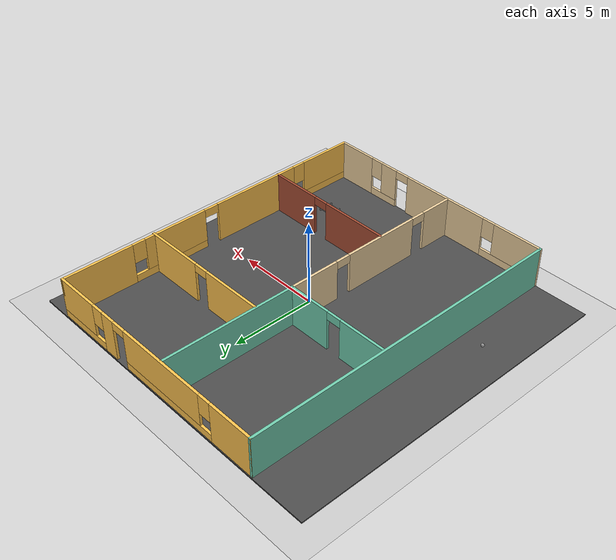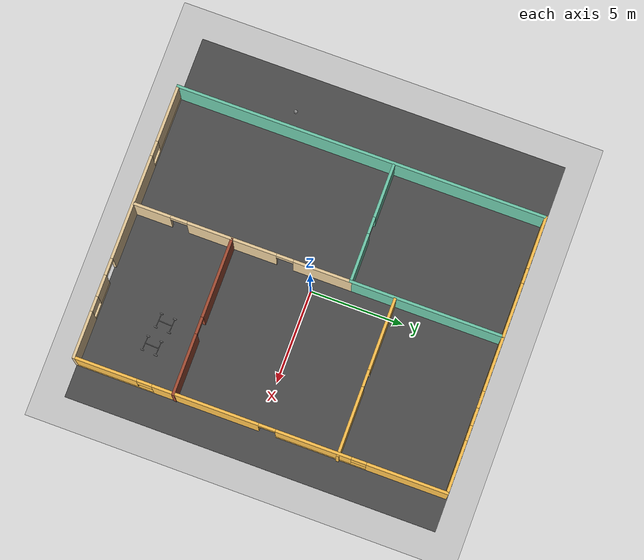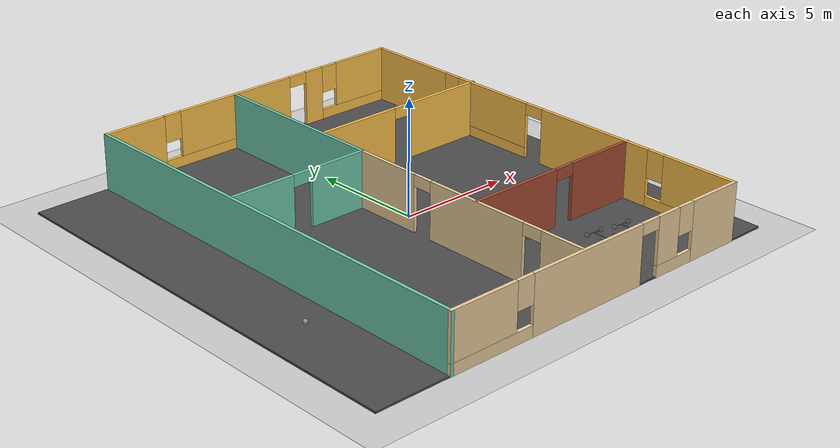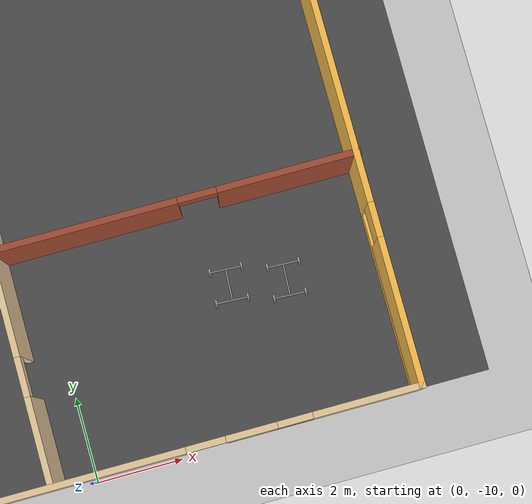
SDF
<sdf version="1.6">
 <world name="default">
  <plugin name="welcome" filename="libwelcome.so"/>
  <light name="sun" type="directional">
   <pose>0 0 10 0 -0 0</pose>
   <diffuse>0.8 0.8 0.8 1</diffuse>
   <specular>0.2 0.2 0.2 1</specular>
   <attenuation>
    <range>1000</range>
    <constant>0.9</constant>
    <linear>0.01</linear>
    <quadratic>0.001</quadratic>
   </attenuation>
   <direction>-0.5 0.1 -0.9</direction>
  </light>
  <model name="ground_plane">
   <static>1</static>
   <link name="link">
    <collision name="collision">
     <geometry><plane><normal>0 0 1</normal><size>100 100</size></plane></geometry>
     <surface>
      <contact><collide_bitmask>65535</collide_bitmask></contact>
      <friction><ode><mu>100</mu><mu2>50</mu2></ode></friction>
     </surface>
    </collision>
    <visual name="visual">
     <cast_shadows>0</cast_shadows>
     <geometry><plane><normal>0 0 1</normal><size>100 100</size></plane></geometry>
     <material>
      <script><uri>file://media/materials/scripts/gazebo.material</uri><name>Gazebo/Grey</name></script>
     </material>
    </visual>
   </link>
  </model>
  <gravity>0 0 -9.8</gravity>
  <magnetic_field>6e-06 2.3e-05 -4.2e-05</magnetic_field>
  <atmosphere type="adiabatic"/>
  <physics name="default_physics" default="0" type="ode">
   <max_step_size>0.001</max_step_size>
   <real_time_factor>1</real_time_factor>
   <real_time_update_rate>1000</real_time_update_rate>
  </physics>
  <scene><ambient>0.4 0.4 0.4 1</ambient><background>0.7 0.7 0.7 1</background><shadows>1</shadows></scene>
  <spherical_coordinates>
   <surface_model>EARTH_WGS84</surface_model>
   <latitude_deg>0</latitude_deg>
   <longitude_deg>0</longitude_deg>
   <elevation>0</elevation>
   <heading_deg>0</heading_deg>
  </spherical_coordinates>
  <model name="TheOffice">
   <pose>0.194983 0.07752 0 0 -0 0</pose>
   <link name="Wall_10">
    <pose>-0.040149 -9.925 0 0 -0 3.14159</pose>
    <visual name="Wall_10_Visual_0">
     <pose>-6.22537 0 1.25 0 -0 0</pose>
     <geometry><box><size>2.54925 0.15 2.5</size></box></geometry>
     <material>
      <script><uri>file://media/materials/scripts/gazebo.material</uri><name>Gazebo/Grey</name></script>
      <ambient>0.921569 0.807843 0.615686 1</ambient>
     </material>
     <meta><layer>0</layer></meta>
    </visual>
    <collision name="Wall_10_Collision_0">
     <geometry><box><size>2.54925 0.15 2.5</size></box></geometry>
     <pose>-6.22537 0 1.25 0 -0 0</pose>
    </collision>
    <visual name="Wall_10_Visual_1">
     <pose>0.736722 0 1.25 0 -0 0</pose>
     <geometry><box><size>5.64147 0.15 2.5</size></box></geometry>
     <material>
      <script><uri>file://media/materials/scripts/gazebo.material</uri><name>Gazebo/Grey</name></script>
      <ambient>0.921569 0.807843 0.615686 1</ambient>
     </material>
     <meta><layer>0</layer></meta>
    </visual>
    <collision name="Wall_10_Collision_1">
     <geometry><box><size>5.64147 0.15 2.5</size></box></geometry>
     <pose>0.736722 0 1.25 0 -0 0</pose>
    </collision>
    <visual name="Wall_10_Visual_2">
     <pose>-3.96738 0 0.25 0 -0 0</pose>
     <geometry><box><size>1.96673 0.15 0.5</size></box></geometry>
     <material>
      <script><uri>file://media/materials/scripts/gazebo.material</uri><name>Gazebo/Grey</name></script>
      <ambient>0.921569 0.807843 0.615686 1</ambient>
     </material>
     <meta><layer>0</layer></meta>
    </visual>
    <collision name="Wall_10_Collision_2">
     <geometry><box><size>1.96673 0.15 0.5</size></box></geometry>
     <pose>-3.96738 0 0.25 0 -0 0</pose>
    </collision>
    <visual name="Wall_10_Visual_3">
     <pose>5.52873 0 0.25 0 -0 0</pose>
     <geometry><box><size>3.94254 0.15 0.5</size></box></geometry>
     <material>
      <script><uri>file://media/materials/scripts/gazebo.material</uri><name>Gazebo/Grey</name></script>
      <ambient>0.921569 0.807843 0.615686 1</ambient>
     </material>
     <meta><layer>0</layer></meta>
    </visual>
    <collision name="Wall_10_Collision_3">
     <geometry><box><size>3.94254 0.15 0.5</size></box></geometry>
     <pose>5.52873 0 0.25 0 -0 0</pose>
    </collision>
    <visual name="Wall_10_Visual_4">
     <pose>-3.56738 0 1.5 0 -0 0</pose>
     <geometry><box><size>1.16673 0.15 2</size></box></geometry>
     <material>
      <script><uri>file://media/materials/scripts/gazebo.material</uri><name>Gazebo/Grey</name></script>
      <ambient>0.921569 0.807843 0.615686 1</ambient>
     </material>
     <meta><layer>0</layer></meta>
    </visual>
    <collision name="Wall_10_Collision_4">
     <geometry><box><size>1.16673 0.15 2</size></box></geometry>
     <pose>-3.56738 0 1.5 0 -0 0</pose>
    </collision>
    <visual name="Wall_10_Visual_5">
     <pose>-3.56738 0 1.5 0 -0 0</pose>
     <geometry><box><size>1.16673 0.15 2</size></box></geometry>
     <material>
      <script><uri>file://media/materials/scripts/gazebo.material</uri><name>Gazebo/Grey</name></script>
      <ambient>0.921569 0.807843 0.615686 1</ambient>
     </material>
     <meta><layer>0</layer></meta>
    </visual>
    <collision name="Wall_10_Collision_5">
     <geometry><box><size>1.16673 0.15 2</size></box></geometry>
     <pose>-3.56738 0 1.5 0 -0 0</pose>
    </collision>
    <visual name="Wall_10_Visual_6">
     <pose>5.92873 0 1.5 0 -0 0</pose>
     <geometry><box><size>3.14254 0.15 2</size></box></geometry>
     <material>
      <script><uri>file://media/materials/scripts/gazebo.material</uri><name>Gazebo/Grey</name></script>
      <ambient>0.921569 0.807843 0.615686 1</ambient>
     </material>
     <meta><layer>0</layer></meta>
    </visual>
    <collision name="Wall_10_Collision_6">
     <geometry><box><size>3.14254 0.15 2</size></box></geometry>
     <pose>5.92873 0 1.5 0 -0 0</pose>
    </collision>
    <visual name="Wall_10_Visual_7">
     <pose>-4.55075 0 1.9 0 -0 0</pose>
     <geometry><box><size>0.8 0.15 1.2</size></box></geometry>
     <material>
      <script><uri>file://media/materials/scripts/gazebo.material</uri><name>Gazebo/Grey</name></script>
      <ambient>0.921569 0.807843 0.615686 1</ambient>
     </material>
     <meta><layer>0</layer></meta>
    </visual>
    <collision name="Wall_10_Collision_7">
     <geometry><box><size>0.8 0.15 1.2</size></box></geometry>
     <pose>-4.55075 0 1.9 0 -0 0</pose>
    </collision>
    <visual name="Wall_10_Visual_8">
     <pose>3.95746 0 1.9 0 -0 0</pose>
     <geometry><box><size>0.8 0.15 1.2</size></box></geometry>
     <material>
      <script><uri>file://media/materials/scripts/gazebo.material</uri><name>Gazebo/Grey</name></script>
      <ambient>0.921569 0.807843 0.615686 1</ambient>
     </material>
     <meta><layer>0</layer></meta>
    </visual>
    <collision name="Wall_10_Collision_8">
     <geometry><box><size>0.8 0.15 1.2</size></box></geometry>
     <pose>3.95746 0 1.9 0 -0 0</pose>
    </collision>
    <visual name="Wall_10_Visual_9">
     <pose>-2.53401 0 2.25 0 -0 0</pose>
     <geometry><box><size>0.9 0.15 0.5</size></box></geometry>
     <material>
      <script><uri>file://media/materials/scripts/gazebo.material</uri><name>Gazebo/Grey</name></script>
      <ambient>0.921569 0.807843 0.615686 1</ambient>
     </material>
     <meta><layer>0</layer></meta>
    </visual>
    <collision name="Wall_10_Collision_9">
     <geometry><box><size>0.9 0.15 0.5</size></box></geometry>
     <pose>-2.53401 0 2.25 0 -0 0</pose>
    </collision>
    <visual name="Wall_10_Visual_10">
     <pose>-2.53401 0 2.25 0 -0 0</pose>
     <geometry><box><size>0.9 0.15 0.5</size></box></geometry>
     <material>
      <script><uri>file://media/materials/scripts/gazebo.material</uri><name>Gazebo/Grey</name></script>
      <ambient>0.921569 0.807843 0.615686 1</ambient>
     </material>
     <meta><layer>0</layer></meta>
    </visual>
    <collision name="Wall_10_Collision_10">
     <geometry><box><size>0.9 0.15 0.5</size></box></geometry>
     <pose>-2.53401 0 2.25 0 -0 0</pose>
    </collision>
   </link>
   <link name="Wall_12">
    <collision name="Wall_12_Collision">
     <geometry><box><size>20 0.15 2.5</size></box></geometry>
     <pose>0 0 1.25 0 -0 0</pose>
    </collision>
    <visual name="Wall_12_Visual">
     <pose>0 0 1.25 0 -0 0</pose>
     <geometry><box><size>20 0.15 2.5</size></box></geometry>
     <material>
      <script><uri>file://media/materials/scripts/gazebo.material</uri><name>Gazebo/Grey</name></script>
      <ambient>0.435294 0.796078 0.67451 1</ambient>
     </material>
     <meta><layer>0</layer></meta>
    </visual>
    <pose>-7.46515 0 0 0 -0 1.5708</pose>
   </link>
   <link name="Wall_14">
    <pose>-0.040149 9.925 0 0 -0 0</pose>
    <visual name="Wall_14_Visual_0">
     <pose>-6.05843 0 1.25 0 -0 0</pose>
     <geometry><box><size>2.88314 0.15 2.5</size></box></geometry>
     <material>
      <script><uri>file://media/materials/scripts/gazebo.material</uri><name>Gazebo/Grey</name></script>
      <ambient>1 0.764706 0.305882 1</ambient>
     </material>
     <meta><layer>0</layer></meta>
    </visual>
    <collision name="Wall_14_Collision_0">
     <geometry><box><size>2.88314 0.15 2.5</size></box></geometry>
     <pose>-6.05843 0 1.25 0 -0 0</pose>
    </collision>
    <visual name="Wall_14_Visual_1">
     <pose>3.37201 0 1.25 0 -0 0</pose>
     <geometry><box><size>0.93492 0.15 2.5</size></box></geometry>
     <material>
      <script><uri>file://media/materials/scripts/gazebo.material</uri><name>Gazebo/Grey</name></script>
      <ambient>1 0.764706 0.305882 1</ambient>
     </material>
     <meta><layer>0</layer></meta>
    </visual>
    <collision name="Wall_14_Collision_1">
     <geometry><box><size>0.93492 0.15 2.5</size></box></geometry>
     <pose>3.37201 0 1.25 0 -0 0</pose>
    </collision>
    <visual name="Wall_14_Visual_2">
     <pose>-1.30615 0 0.25 0 -0 0</pose>
     <geometry><box><size>6.62141 0.15 0.5</size></box></geometry>
     <material>
      <script><uri>file://media/materials/scripts/gazebo.material</uri><name>Gazebo/Grey</name></script>
      <ambient>1 0.764706 0.305882 1</ambient>
     </material>
     <meta><layer>0</layer></meta>
    </visual>
    <collision name="Wall_14_Collision_2">
     <geometry><box><size>6.62141 0.15 0.5</size></box></geometry>
     <pose>-1.30615 0 0.25 0 -0 0</pose>
    </collision>
    <visual name="Wall_14_Visual_3">
     <pose>5.66974 0 0.25 0 -0 0</pose>
     <geometry><box><size>3.66053 0.15 0.5</size></box></geometry>
     <material>
      <script><uri>file://media/materials/scripts/gazebo.material</uri><name>Gazebo/Grey</name></script>
      <ambient>1 0.764706 0.305882 1</ambient>
     </material>
     <meta><layer>0</layer></meta>
    </visual>
    <collision name="Wall_14_Collision_3">
     <geometry><box><size>3.66053 0.15 0.5</size></box></geometry>
     <pose>5.66974 0 0.25 0 -0 0</pose>
    </collision>
    <visual name="Wall_14_Visual_4">
     <pose>-0.906151 0 1.5 0 -0 0</pose>
     <geometry><box><size>5.82141 0.15 2</size></box></geometry>
     <material>
      <script><uri>file://media/materials/scripts/gazebo.material</uri><name>Gazebo/Grey</name></script>
      <ambient>1 0.764706 0.305882 1</ambient>
     </material>
     <meta><layer>0</layer></meta>
    </visual>
    <collision name="Wall_14_Collision_4">
     <geometry><box><size>5.82141 0.15 2</size></box></geometry>
     <pose>-0.906151 0 1.5 0 -0 0</pose>
    </collision>
    <visual name="Wall_14_Visual_5">
     <pose>-0.906151 0 1.5 0 -0 0</pose>
     <geometry><box><size>5.82141 0.15 2</size></box></geometry>
     <material>
      <script><uri>file://media/materials/scripts/gazebo.material</uri><name>Gazebo/Grey</name></script>
      <ambient>1 0.764706 0.305882 1</ambient>
     </material>
     <meta><layer>0</layer></meta>
    </visual>
    <collision name="Wall_14_Collision_5">
     <geometry><box><size>5.82141 0.15 2</size></box></geometry>
     <pose>-0.906151 0 1.5 0 -0 0</pose>
    </collision>
    <visual name="Wall_14_Visual_6">
     <pose>6.06974 0 1.5 0 -0 0</pose>
     <geometry><box><size>2.86053 0.15 2</size></box></geometry>
     <material>
      <script><uri>file://media/materials/scripts/gazebo.material</uri><name>Gazebo/Grey</name></script>
      <ambient>1 0.764706 0.305882 1</ambient>
     </material>
     <meta><layer>0</layer></meta>
    </visual>
    <collision name="Wall_14_Collision_6">
     <geometry><box><size>2.86053 0.15 2</size></box></geometry>
     <pose>6.06974 0 1.5 0 -0 0</pose>
    </collision>
    <visual name="Wall_14_Visual_7">
     <pose>-4.21685 0 1.9 0 -0 0</pose>
     <geometry><box><size>0.8 0.15 1.2</size></box></geometry>
     <material>
      <script><uri>file://media/materials/scripts/gazebo.material</uri><name>Gazebo/Grey</name></script>
      <ambient>1 0.764706 0.305882 1</ambient>
     </material>
     <meta><layer>0</layer></meta>
    </visual>
    <collision name="Wall_14_Collision_7">
     <geometry><box><size>0.8 0.15 1.2</size></box></geometry>
     <pose>-4.21685 0 1.9 0 -0 0</pose>
    </collision>
    <visual name="Wall_14_Visual_8">
     <pose>4.23947 0 1.9 0 -0 0</pose>
     <geometry><box><size>0.8 0.15 1.2</size></box></geometry>
     <material>
      <script><uri>file://media/materials/scripts/gazebo.material</uri><name>Gazebo/Grey</name></script>
      <ambient>1 0.764706 0.305882 1</ambient>
     </material>
     <meta><layer>0</layer></meta>
    </visual>
    <collision name="Wall_14_Collision_8">
     <geometry><box><size>0.8 0.15 1.2</size></box></geometry>
     <pose>4.23947 0 1.9 0 -0 0</pose>
    </collision>
    <visual name="Wall_14_Visual_9">
     <pose>2.45455 0 2.25 0 -0 0</pose>
     <geometry><box><size>0.9 0.15 0.5</size></box></geometry>
     <material>
      <script><uri>file://media/materials/scripts/gazebo.material</uri><name>Gazebo/Grey</name></script>
      <ambient>1 0.764706 0.305882 1</ambient>
     </material>
     <meta><layer>0</layer></meta>
    </visual>
    <collision name="Wall_14_Collision_9">
     <geometry><box><size>0.9 0.15 0.5</size></box></geometry>
     <pose>2.45455 0 2.25 0 -0 0</pose>
    </collision>
    <visual name="Wall_14_Visual_10">
     <pose>2.45455 0 2.25 0 -0 0</pose>
     <geometry><box><size>0.9 0.15 0.5</size></box></geometry>
     <material>
      <script><uri>file://media/materials/scripts/gazebo.material</uri><name>Gazebo/Grey</name></script>
      <ambient>1 0.764706 0.305882 1</ambient>
     </material>
     <meta><layer>0</layer></meta>
    </visual>
    <collision name="Wall_14_Collision_10">
     <geometry><box><size>0.9 0.15 0.5</size></box></geometry>
     <pose>2.45455 0 2.25 0 -0 0</pose>
    </collision>
   </link>
   <link name="Wall_15">
    <pose>7.38485 0 0 0 0 -1.5708</pose>
    <visual name="Wall_15_Visual_0">
     <pose>-7.83118 0 1.25 0 -0 0</pose>
     <geometry><box><size>4.33764 0.15 2.5</size></box></geometry>
     <material>
      <script><uri>file://media/materials/scripts/gazebo.material</uri><name>Gazebo/Grey</name></script>
      <ambient>1 0.764706 0.305882 1</ambient>
     </material>
     <meta><layer>0</layer></meta>
    </visual>
    <collision name="Wall_15_Collision_0">
     <geometry><box><size>4.33764 0.15 2.5</size></box></geometry>
     <pose>-7.83118 0 1.25 0 -0 0</pose>
    </collision>
    <visual name="Wall_15_Visual_1">
     <pose>2.90769 0 1.25 0 -0 0</pose>
     <geometry><box><size>5.68679 0.15 2.5</size></box></geometry>
     <material>
      <script><uri>file://media/materials/scripts/gazebo.material</uri><name>Gazebo/Grey</name></script>
      <ambient>1 0.764706 0.305882 1</ambient>
     </material>
     <meta><layer>0</layer></meta>
    </visual>
    <collision name="Wall_15_Collision_1">
     <geometry><box><size>5.68679 0.15 2.5</size></box></geometry>
     <pose>2.90769 0 1.25 0 -0 0</pose>
    </collision>
    <visual name="Wall_15_Visual_2">
     <pose>-3.24903 0 0.25 0 -0 0</pose>
     <geometry><box><size>4.82665 0.15 0.5</size></box></geometry>
     <material>
      <script><uri>file://media/materials/scripts/gazebo.material</uri><name>Gazebo/Grey</name></script>
      <ambient>1 0.764706 0.305882 1</ambient>
     </material>
     <meta><layer>0</layer></meta>
    </visual>
    <collision name="Wall_15_Collision_2">
     <geometry><box><size>4.82665 0.15 0.5</size></box></geometry>
     <pose>-3.24903 0 0.25 0 -0 0</pose>
    </collision>
    <visual name="Wall_15_Visual_3">
     <pose>7.87554 0 0.25 0 -0 0</pose>
     <geometry><box><size>4.24891 0.15 0.5</size></box></geometry>
     <material>
      <script><uri>file://media/materials/scripts/gazebo.material</uri><name>Gazebo/Grey</name></script>
      <ambient>1 0.764706 0.305882 1</ambient>
     </material>
     <meta><layer>0</layer></meta>
    </visual>
    <collision name="Wall_15_Collision_3">
     <geometry><box><size>4.24891 0.15 0.5</size></box></geometry>
     <pose>7.87554 0 0.25 0 -0 0</pose>
    </collision>
    <visual name="Wall_15_Visual_4">
     <pose>-2.84903 0 1.5 0 -0 0</pose>
     <geometry><box><size>4.02665 0.15 2</size></box></geometry>
     <material>
      <script><uri>file://media/materials/scripts/gazebo.material</uri><name>Gazebo/Grey</name></script>
      <ambient>1 0.764706 0.305882 1</ambient>
     </material>
     <meta><layer>0</layer></meta>
    </visual>
    <collision name="Wall_15_Collision_4">
     <geometry><box><size>4.02665 0.15 2</size></box></geometry>
     <pose>-2.84903 0 1.5 0 -0 0</pose>
    </collision>
    <visual name="Wall_15_Visual_5">
     <pose>-2.84903 0 1.5 0 -0 0</pose>
     <geometry><box><size>4.02665 0.15 2</size></box></geometry>
     <material>
      <script><uri>file://media/materials/scripts/gazebo.material</uri><name>Gazebo/Grey</name></script>
      <ambient>1 0.764706 0.305882 1</ambient>
     </material>
     <meta><layer>0</layer></meta>
    </visual>
    <collision name="Wall_15_Collision_5">
     <geometry><box><size>4.02665 0.15 2</size></box></geometry>
     <pose>-2.84903 0 1.5 0 -0 0</pose>
    </collision>
    <visual name="Wall_15_Visual_6">
     <pose>8.27554 0 1.5 0 -0 0</pose>
     <geometry><box><size>3.44891 0.15 2</size></box></geometry>
     <material>
      <script><uri>file://media/materials/scripts/gazebo.material</uri><name>Gazebo/Grey</name></script>
      <ambient>1 0.764706 0.305882 1</ambient>
     </material>
     <meta><layer>0</layer></meta>
    </visual>
    <collision name="Wall_15_Collision_6">
     <geometry><box><size>3.44891 0.15 2</size></box></geometry>
     <pose>8.27554 0 1.5 0 -0 0</pose>
    </collision>
    <visual name="Wall_15_Visual_7">
     <pose>-5.26236 0 1.9 0 -0 0</pose>
     <geometry><box><size>0.8 0.15 1.2</size></box></geometry>
     <material>
      <script><uri>file://media/materials/scripts/gazebo.material</uri><name>Gazebo/Grey</name></script>
      <ambient>1 0.764706 0.305882 1</ambient>
     </material>
     <meta><layer>0</layer></meta>
    </visual>
    <collision name="Wall_15_Collision_7">
     <geometry><box><size>0.8 0.15 1.2</size></box></geometry>
     <pose>-5.26236 0 1.9 0 -0 0</pose>
    </collision>
    <visual name="Wall_15_Visual_8">
     <pose>6.15109 0 1.9 0 -0 0</pose>
     <geometry><box><size>0.8 0.15 1.2</size></box></geometry>
     <material>
      <script><uri>file://media/materials/scripts/gazebo.material</uri><name>Gazebo/Grey</name></script>
      <ambient>1 0.764706 0.305882 1</ambient>
     </material>
     <meta><layer>0</layer></meta>
    </visual>
    <collision name="Wall_15_Collision_8">
     <geometry><box><size>0.8 0.15 1.2</size></box></geometry>
     <pose>6.15109 0 1.9 0 -0 0</pose>
    </collision>
    <visual name="Wall_15_Visual_9">
     <pose>-0.385703 0 2.25 0 -0 0</pose>
     <geometry><box><size>0.9 0.15 0.5</size></box></geometry>
     <material>
      <script><uri>file://media/materials/scripts/gazebo.material</uri><name>Gazebo/Grey</name></script>
      <ambient>1 0.764706 0.305882 1</ambient>
     </material>
     <meta><layer>0</layer></meta>
    </visual>
    <collision name="Wall_15_Collision_9">
     <geometry><box><size>0.9 0.15 0.5</size></box></geometry>
     <pose>-0.385703 0 2.25 0 -0 0</pose>
    </collision>
    <visual name="Wall_15_Visual_10">
     <pose>-0.385703 0 2.25 0 -0 0</pose>
     <geometry><box><size>0.9 0.15 0.5</size></box></geometry>
     <material>
      <script><uri>file://media/materials/scripts/gazebo.material</uri><name>Gazebo/Grey</name></script>
      <ambient>1 0.764706 0.305882 1</ambient>
     </material>
     <meta><layer>0</layer></meta>
    </visual>
    <collision name="Wall_15_Collision_10">
     <geometry><box><size>0.9 0.15 0.5</size></box></geometry>
     <pose>-0.385703 0 2.25 0 -0 0</pose>
    </collision>
   </link>
   <link name="Wall_18">
    <collision name="Wall_18_Collision">
     <geometry><box><size>8.25 0.15 2.5</size></box></geometry>
     <pose>0 0 1.25 0 -0 0</pose>
    </collision>
    <visual name="Wall_18_Visual">
     <pose>0 0 1.25 0 -0 0</pose>
     <geometry><box><size>8.25 0.15 2.5</size></box></geometry>
     <material>
      <script><uri>file://media/materials/scripts/gazebo.material</uri><name>Gazebo/Grey</name></script>
      <ambient>0.435294 0.796078 0.67451 1</ambient>
     </material>
     <meta><layer>0</layer></meta>
    </visual>
    <pose>-0.988608 5.83138 0 0 0 -1.5708</pose>
   </link>
   <link name="Wall_19">
    <pose>-4.16361 1.78138 0 0 -0 3.14159</pose>
    <visual name="Wall_19_Visual_0">
     <pose>-1.90706 0 1.25 0 -0 0</pose>
     <geometry><box><size>2.68588 0.15 2.5</size></box></geometry>
     <material>
      <script><uri>file://media/materials/scripts/gazebo.material</uri><name>Gazebo/Grey</name></script>
      <ambient>0.435294 0.796078 0.67451 1</ambient>
     </material>
     <meta><layer>0</layer></meta>
    </visual>
    <collision name="Wall_19_Collision_0">
     <geometry><box><size>2.68588 0.15 2.5</size></box></geometry>
     <pose>-1.90706 0 1.25 0 -0 0</pose>
    </collision>
    <visual name="Wall_19_Visual_1">
     <pose>1.79294 0 1.25 0 -0 0</pose>
     <geometry><box><size>2.91412 0.15 2.5</size></box></geometry>
     <material>
      <script><uri>file://media/materials/scripts/gazebo.material</uri><name>Gazebo/Grey</name></script>
      <ambient>0.435294 0.796078 0.67451 1</ambient>
     </material>
     <meta><layer>0</layer></meta>
    </visual>
    <collision name="Wall_19_Collision_1">
     <geometry><box><size>2.91412 0.15 2.5</size></box></geometry>
     <pose>1.79294 0 1.25 0 -0 0</pose>
    </collision>
    <visual name="Wall_19_Visual_2">
     <pose>-0.11412 0 2.25 0 -0 0</pose>
     <geometry><box><size>0.9 0.15 0.5</size></box></geometry>
     <material>
      <script><uri>file://media/materials/scripts/gazebo.material</uri><name>Gazebo/Grey</name></script>
      <ambient>0.435294 0.796078 0.67451 1</ambient>
     </material>
     <meta><layer>0</layer></meta>
    </visual>
    <collision name="Wall_19_Collision_2">
     <geometry><box><size>0.9 0.15 0.5</size></box></geometry>
     <pose>-0.11412 0 2.25 0 -0 0</pose>
    </collision>
   </link>
   <link name="Wall_22">
    <pose>-0.988608 -4.01862 0 0 0 -1.5708</pose>
    <visual name="Wall_22_Visual_0">
     <pose>-4.30202 0 1.25 0 -0 0</pose>
     <geometry><box><size>3.14597 0.15 2.5</size></box></geometry>
     <material>
      <script><uri>file://media/materials/scripts/gazebo.material</uri><name>Gazebo/Grey</name></script>
      <ambient>0.921569 0.807843 0.615686 1</ambient>
     </material>
     <meta><layer>0</layer></meta>
    </visual>
    <collision name="Wall_22_Collision_0">
     <geometry><box><size>3.14597 0.15 2.5</size></box></geometry>
     <pose>-4.30202 0 1.25 0 -0 0</pose>
    </collision>
    <visual name="Wall_22_Visual_1">
     <pose>0.574328 0 1.25 0 -0 0</pose>
     <geometry><box><size>4.80672 0.15 2.5</size></box></geometry>
     <material>
      <script><uri>file://media/materials/scripts/gazebo.material</uri><name>Gazebo/Grey</name></script>
      <ambient>0.921569 0.807843 0.615686 1</ambient>
     </material>
     <meta><layer>0</layer></meta>
    </visual>
    <collision name="Wall_22_Collision_1">
     <geometry><box><size>4.80672 0.15 2.5</size></box></geometry>
     <pose>0.574328 0 1.25 0 -0 0</pose>
    </collision>
    <visual name="Wall_22_Visual_2">
     <pose>4.87634 0 1.25 0 -0 0</pose>
     <geometry><box><size>1.99731 0.15 2.5</size></box></geometry>
     <material>
      <script><uri>file://media/materials/scripts/gazebo.material</uri><name>Gazebo/Grey</name></script>
      <ambient>0.921569 0.807843 0.615686 1</ambient>
     </material>
     <meta><layer>0</layer></meta>
    </visual>
    <collision name="Wall_22_Collision_2">
     <geometry><box><size>1.99731 0.15 2.5</size></box></geometry>
     <pose>4.87634 0 1.25 0 -0 0</pose>
    </collision>
    <visual name="Wall_22_Visual_3">
     <pose>-2.27903 0 2.25 0 -0 0</pose>
     <geometry><box><size>0.9 0.15 0.5</size></box></geometry>
     <material>
      <script><uri>file://media/materials/scripts/gazebo.material</uri><name>Gazebo/Grey</name></script>
      <ambient>0.921569 0.807843 0.615686 1</ambient>
     </material>
     <meta><layer>0</layer></meta>
    </visual>
    <collision name="Wall_22_Collision_3">
     <geometry><box><size>0.9 0.15 0.5</size></box></geometry>
     <pose>-2.27903 0 2.25 0 -0 0</pose>
    </collision>
    <visual name="Wall_22_Visual_4">
     <pose>3.42769 0 2.25 0 -0 0</pose>
     <geometry><box><size>0.9 0.15 0.5</size></box></geometry>
     <material>
      <script><uri>file://media/materials/scripts/gazebo.material</uri><name>Gazebo/Grey</name></script>
      <ambient>0.921569 0.807843 0.615686 1</ambient>
     </material>
     <meta><layer>0</layer></meta>
    </visual>
    <collision name="Wall_22_Collision_4">
     <geometry><box><size>0.9 0.15 0.5</size></box></geometry>
     <pose>3.42769 0 2.25 0 -0 0</pose>
    </collision>
   </link>
   <link name="Wall_24">
    <pose>3.29015 4.17465 0 0 -0 0</pose>
    <visual name="Wall_24_Visual_0">
     <pose>-2.31045 0 1.25 0 -0 0</pose>
     <geometry><box><size>3.8791 0.15 2.5</size></box></geometry>
     <material>
      <script><uri>file://media/materials/scripts/gazebo.material</uri><name>Gazebo/Grey</name></script>
      <ambient>1 0.764706 0.305882 1</ambient>
     </material>
     <meta><layer>0</layer></meta>
    </visual>
    <collision name="Wall_24_Collision_0">
     <geometry><box><size>3.8791 0.15 2.5</size></box></geometry>
     <pose>-2.31045 0 1.25 0 -0 0</pose>
    </collision>
    <visual name="Wall_24_Visual_1">
     <pose>2.38955 0 1.25 0 -0 0</pose>
     <geometry><box><size>3.7209 0.15 2.5</size></box></geometry>
     <material>
      <script><uri>file://media/materials/scripts/gazebo.material</uri><name>Gazebo/Grey</name></script>
      <ambient>1 0.764706 0.305882 1</ambient>
     </material>
     <meta><layer>0</layer></meta>
    </visual>
    <collision name="Wall_24_Collision_1">
     <geometry><box><size>3.7209 0.15 2.5</size></box></geometry>
     <pose>2.38955 0 1.25 0 -0 0</pose>
    </collision>
    <visual name="Wall_24_Visual_2">
     <pose>0.079103 0 2.25 0 -0 0</pose>
     <geometry><box><size>0.9 0.15 0.5</size></box></geometry>
     <material>
      <script><uri>file://media/materials/scripts/gazebo.material</uri><name>Gazebo/Grey</name></script>
      <ambient>1 0.764706 0.305882 1</ambient>
     </material>
     <meta><layer>0</layer></meta>
    </visual>
    <collision name="Wall_24_Collision_2">
     <geometry><box><size>0.9 0.15 0.5</size></box></geometry>
     <pose>0.079103 0 2.25 0 -0 0</pose>
    </collision>
   </link>
   <link name="Wall_26">
    <pose>3.23827 -4.59295 0 0 -0 0</pose>
    <visual name="Wall_26_Visual_0">
     <pose>-2.10293 0 1.25 0 -0 0</pose>
     <geometry><box><size>4.29414 0.15 2.5</size></box></geometry>
     <material>
      <script><uri>file://media/materials/scripts/gazebo.material</uri><name>Gazebo/Bricks</name></script>
      <ambient>1 0.764706 0.305882 1</ambient>
     </material>
     <meta><layer>0</layer></meta>
    </visual>
    <collision name="Wall_26_Collision_0">
     <geometry><box><size>4.29414 0.15 2.5</size></box></geometry>
     <pose>-2.10293 0 1.25 0 -0 0</pose>
    </collision>
    <visual name="Wall_26_Visual_1">
     <pose>2.59707 0 1.25 0 -0 0</pose>
     <geometry><box><size>3.30586 0.15 2.5</size></box></geometry>
     <material>
      <script><uri>file://media/materials/scripts/gazebo.material</uri><name>Gazebo/Bricks</name></script>
      <ambient>1 0.764706 0.305882 1</ambient>
     </material>
     <meta><layer>0</layer></meta>
    </visual>
    <collision name="Wall_26_Collision_1">
     <geometry><box><size>3.30586 0.15 2.5</size></box></geometry>
     <pose>2.59707 0 1.25 0 -0 0</pose>
    </collision>
    <visual name="Wall_26_Visual_2">
     <pose>0.494138 0 2.25 0 -0 0</pose>
     <geometry><box><size>0.9 0.15 0.5</size></box></geometry>
     <material>
      <script><uri>file://media/materials/scripts/gazebo.material</uri><name>Gazebo/Bricks</name></script>
      <ambient>1 0.764706 0.305882 1</ambient>
     </material>
     <meta><layer>0</layer></meta>
    </visual>
    <collision name="Wall_26_Collision_2">
     <geometry><box><size>0.9 0.15 0.5</size></box></geometry>
     <pose>0.494138 0 2.25 0 -0 0</pose>
    </collision>
   </link>
   <static>1</static>
  </model>
  <model name="Environment_0">
   <model name="asphalt_plane">
    <static>1</static>
    <link name="link">
     <collision name="collision"><geometry><box><size>20 20 0.1</size></box></geometry></collision>
     <visual name="visual">
      <cast_shadows>0</cast_shadows>
      <geometry><box><size>20 20 0.1</size></box></geometry>
      <material>
       <script>
        <uri>model://asphalt_plane/materials/scripts</uri>
        <uri>model://asphalt_plane/materials/textures</uri>
        <name>vrc/asphalt</name>
       </script>
      </material>
     </visual>
    </link>
   </model>
   <static>0</static>
   <pose>-0.611145 0.123266 0 0 -0 0</pose>
  </model>
  <model name="RobotModel">
   <link name="link_2_clone">
    <pose>10.2602 -7.39566 0.5 -1.57203 1.5707 3.14035</pose>
    <inertial>
     <mass>1</mass>
     <inertia><ixx>0.145833</ixx><ixy>0</ixy><ixz>0</ixz><iyy>0.145833</iyy><iyz>0</iyz><izz>0.125</izz></inertia>
    </inertial>
    <visual name="visual">
     <geometry><cylinder><radius>0.02</radius><length>0.7</length></cylinder></geometry>
     <material>
      <lighting>1</lighting>
      <script><uri>file://media/materials/scripts/gazebo.material</uri><name>Gazebo/Grey</name></script>
      <shader type="pixel"><normal_map>__default__</normal_map></shader>
      <ambient>0.3 0.3 0.3 1</ambient>
      <diffuse>0.7 0.7 0.7 1</diffuse>
      <specular>0.01 0.01 0.01 1</specular>
      <emissive>0 0 0 1</emissive>
     </material>
    </visual>
    <collision name="collision">
     <geometry><cylinder><radius>0.02</radius><length>0.7</length></cylinder></geometry>
     <surface>
      <friction>
       <ode><mu>1</mu><mu2>1</mu2><fdir1>0 0 0</fdir1><slip1>0</slip1><slip2>0</slip2></ode>
       <torsional>
        <coefficient>1</coefficient>
        <patch_radius>0</patch_radius>
        <surface_radius>0</surface_radius>
        <use_patch_radius>1</use_patch_radius>
        <ode><slip>0</slip></ode>
       </torsional>
      </friction>
      <bounce><restitution_coefficient>0</restitution_coefficient><threshold>1e+06</threshold></bounce>
      <contact>
       <collide_without_contact>0</collide_without_contact>
       <collide_without_contact_bitmask>1</collide_without_contact_bitmask>
       <collide_bitmask>1</collide_bitmask>
       <ode>
        <soft_cfm>0</soft_cfm>
        <soft_erp>0.2</soft_erp>
        <kp>1e+13</kp>
        <kd>1</kd>
        <max_vel>0.01</max_vel>
        <min_depth>0</min_depth>
       </ode>
       <bullet>
        <split_impulse>1</split_impulse>
        <split_impulse_penetration_threshold>-0.01</split_impulse_penetration_threshold>
        <soft_cfm>0</soft_cfm>
        <soft_erp>0.2</soft_erp>
        <kp>1e+13</kp>
        <kd>1</kd>
       </bullet>
      </contact>
     </surface>
    </collision>
   </link>
   <link name="link_2_clone_0">
    <pose>10.2602 -7.76566 0.5 -3.14159 1.5707 -3.14159</pose>
    <inertial>
     <mass>1</mass>
     <inertia><ixx>0.145833</ixx><ixy>0</ixy><ixz>0</ixz><iyy>0.145833</iyy><iyz>0</iyz><izz>0.125</izz></inertia>
    </inertial>
    <visual name="visual">
     <geometry><cylinder><radius>0.02</radius><length>0.7</length></cylinder></geometry>
     <material>
      <lighting>1</lighting>
      <script><uri>file://media/materials/scripts/gazebo.material</uri><name>Gazebo/Grey</name></script>
      <shader type="pixel"><normal_map>__default__</normal_map></shader>
      <ambient>0.3 0.3 0.3 1</ambient>
      <diffuse>0.7 0.7 0.7 1</diffuse>
      <specular>0.01 0.01 0.01 1</specular>
      <emissive>0 0 0 1</emissive>
     </material>
    </visual>
    <collision name="collision">
     <geometry><cylinder><radius>0.02</radius><length>0.7</length></cylinder></geometry>
     <surface>
      <friction>
       <ode><mu>1</mu><mu2>1</mu2><fdir1>0 0 0</fdir1><slip1>0</slip1><slip2>0</slip2></ode>
       <torsional>
        <coefficient>1</coefficient>
        <patch_radius>0</patch_radius>
        <surface_radius>0</surface_radius>
        <use_patch_radius>1</use_patch_radius>
        <ode><slip>0</slip></ode>
       </torsional>
      </friction>
      <bounce><restitution_coefficient>0</restitution_coefficient><threshold>1e+06</threshold></bounce>
      <contact>
       <collide_without_contact>0</collide_without_contact>
       <collide_without_contact_bitmask>1</collide_without_contact_bitmask>
       <collide_bitmask>1</collide_bitmask>
       <ode>
        <soft_cfm>0</soft_cfm>
        <soft_erp>0.2</soft_erp>
        <kp>1e+13</kp>
        <kd>1</kd>
        <max_vel>0.01</max_vel>
        <min_depth>0</min_depth>
       </ode>
       <bullet>
        <split_impulse>1</split_impulse>
        <split_impulse_penetration_threshold>-0.01</split_impulse_penetration_threshold>
        <soft_cfm>0</soft_cfm>
        <soft_erp>0.2</soft_erp>
        <kp>1e+13</kp>
        <kd>1</kd>
       </bullet>
      </contact>
     </surface>
    </collision>
   </link>
   <link name="link_2_clone_0_clone">
    <pose>10.6352 -7.76566 0.5 -3.14159 1.5707 -3.14159</pose>
    <inertial>
     <mass>1</mass>
     <inertia><ixx>0.145833</ixx><ixy>0</ixy><ixz>0</ixz><iyy>0.145833</iyy><iyz>0</iyz><izz>0.125</izz></inertia>
    </inertial>
    <visual name="visual">
     <geometry><cylinder><radius>0.1</radius><length>0.05</length></cylinder></geometry>
     <material>
      <lighting>1</lighting>
      <script><uri>file://media/materials/scripts/gazebo.material</uri><name>Gazebo/Grey</name></script>
      <shader type="pixel"><normal_map>__default__</normal_map></shader>
      <ambient>0.3 0.3 0.3 1</ambient>
      <diffuse>0.7 0.7 0.7 1</diffuse>
      <specular>0.01 0.01 0.01 1</specular>
      <emissive>0 0 0 1</emissive>
     </material>
    </visual>
    <collision name="collision">
     <geometry><cylinder><radius>0.1</radius><length>0.05</length></cylinder></geometry>
     <surface>
      <friction>
       <ode><mu>1</mu><mu2>1</mu2><fdir1>0 0 0</fdir1><slip1>0</slip1><slip2>0</slip2></ode>
       <torsional>
        <coefficient>1</coefficient>
        <patch_radius>0</patch_radius>
        <surface_radius>0</surface_radius>
        <use_patch_radius>1</use_patch_radius>
        <ode><slip>0</slip></ode>
       </torsional>
      </friction>
      <bounce><restitution_coefficient>0</restitution_coefficient><threshold>1e+06</threshold></bounce>
      <contact>
       <collide_without_contact>0</collide_without_contact>
       <collide_without_contact_bitmask>1</collide_without_contact_bitmask>
       <collide_bitmask>1</collide_bitmask>
       <ode>
        <soft_cfm>0</soft_cfm>
        <soft_erp>0.2</soft_erp>
        <kp>1e+13</kp>
        <kd>1</kd>
        <max_vel>0.01</max_vel>
        <min_depth>0</min_depth>
       </ode>
       <bullet>
        <split_impulse>1</split_impulse>
        <split_impulse_penetration_threshold>-0.01</split_impulse_penetration_threshold>
        <soft_cfm>0</soft_cfm>
        <soft_erp>0.2</soft_erp>
        <kp>1e+13</kp>
        <kd>1</kd>
       </bullet>
      </contact>
     </surface>
    </collision>
   </link>
   <link name="link_2_clone_0_clone_0">
    <pose>10.2602 -7.02566 0.5 -3.14159 1.5707 -3.14159</pose>
    <inertial>
     <mass>1</mass>
     <inertia><ixx>0.145833</ixx><ixy>0</ixy><ixz>0</ixz><iyy>0.145833</iyy><iyz>0</iyz><izz>0.125</izz></inertia>
    </inertial>
    <visual name="visual">
     <geometry><cylinder><radius>0.02</radius><length>0.7</length></cylinder></geometry>
     <material>
      <lighting>1</lighting>
      <script><uri>file://media/materials/scripts/gazebo.material</uri><name>Gazebo/Grey</name></script>
      <shader type="pixel"><normal_map>__default__</normal_map></shader>
      <ambient>0.3 0.3 0.3 1</ambient>
      <diffuse>0.7 0.7 0.7 1</diffuse>
      <specular>0.01 0.01 0.01 1</specular>
      <emissive>0 0 0 1</emissive>
     </material>
    </visual>
    <collision name="collision">
     <geometry><cylinder><radius>0.02</radius><length>0.7</length></cylinder></geometry>
     <surface>
      <friction>
       <ode><mu>1</mu><mu2>1</mu2><fdir1>0 0 0</fdir1><slip1>0</slip1><slip2>0</slip2></ode>
       <torsional>
        <coefficient>1</coefficient>
        <patch_radius>0</patch_radius>
        <surface_radius>0</surface_radius>
        <use_patch_radius>1</use_patch_radius>
        <ode><slip>0</slip></ode>
       </torsional>
      </friction>
      <bounce><restitution_coefficient>0</restitution_coefficient><threshold>1e+06</threshold></bounce>
      <contact>
       <collide_without_contact>0</collide_without_contact>
       <collide_without_contact_bitmask>1</collide_without_contact_bitmask>
       <collide_bitmask>1</collide_bitmask>
       <ode>
        <soft_cfm>0</soft_cfm>
        <soft_erp>0.2</soft_erp>
        <kp>1e+13</kp>
        <kd>1</kd>
        <max_vel>0.01</max_vel>
        <min_depth>0</min_depth>
       </ode>
       <bullet>
        <split_impulse>1</split_impulse>
        <split_impulse_penetration_threshold>-0.01</split_impulse_penetration_threshold>
        <soft_cfm>0</soft_cfm>
        <soft_erp>0.2</soft_erp>
        <kp>1e+13</kp>
        <kd>1</kd>
       </bullet>
      </contact>
     </surface>
    </collision>
   </link>
   <link name="link_2_clone_0_clone_clone_0">
    <pose>10.6352 -7.02566 0.5 -3.14159 1.5707 -3.14159</pose>
    <inertial>
     <mass>1</mass>
     <inertia><ixx>0.145833</ixx><ixy>0</ixy><ixz>0</ixz><iyy>0.145833</iyy><iyz>0</iyz><izz>0.125</izz></inertia>
    </inertial>
    <visual name="visual">
     <geometry><cylinder><radius>0.1</radius><length>0.05</length></cylinder></geometry>
     <material>
      <lighting>1</lighting>
      <script><uri>file://media/materials/scripts/gazebo.material</uri><name>Gazebo/Grey</name></script>
      <shader type="pixel"><normal_map>__default__</normal_map></shader>
      <ambient>0.3 0.3 0.3 1</ambient>
      <diffuse>0.7 0.7 0.7 1</diffuse>
      <specular>0.01 0.01 0.01 1</specular>
      <emissive>0 0 0 1</emissive>
     </material>
    </visual>
    <collision name="collision">
     <geometry><cylinder><radius>0.1</radius><length>0.05</length></cylinder></geometry>
     <surface>
      <friction>
       <ode><mu>1</mu><mu2>1</mu2><fdir1>0 0 0</fdir1><slip1>0</slip1><slip2>0</slip2></ode>
       <torsional>
        <coefficient>1</coefficient>
        <patch_radius>0</patch_radius>
        <surface_radius>0</surface_radius>
        <use_patch_radius>1</use_patch_radius>
        <ode><slip>0</slip></ode>
       </torsional>
      </friction>
      <bounce><restitution_coefficient>0</restitution_coefficient><threshold>1e+06</threshold></bounce>
      <contact>
       <collide_without_contact>0</collide_without_contact>
       <collide_without_contact_bitmask>1</collide_without_contact_bitmask>
       <collide_bitmask>1</collide_bitmask>
       <ode>
        <soft_cfm>0</soft_cfm>
        <soft_erp>0.2</soft_erp>
        <kp>1e+13</kp>
        <kd>1</kd>
        <max_vel>0.01</max_vel>
        <min_depth>0</min_depth>
       </ode>
       <bullet>
        <split_impulse>1</split_impulse>
        <split_impulse_penetration_threshold>-0.01</split_impulse_penetration_threshold>
        <soft_cfm>0</soft_cfm>
        <soft_erp>0.2</soft_erp>
        <kp>1e+13</kp>
        <kd>1</kd>
       </bullet>
      </contact>
     </surface>
    </collision>
   </link>
   <link name="link_2_clone_0_clone_clone_0_clone">
    <pose>9.88519 -7.02566 0.5 -3.14159 1.5707 -3.14159</pose>
    <inertial>
     <mass>1</mass>
     <inertia><ixx>0.145833</ixx><ixy>0</ixy><ixz>0</ixz><iyy>0.145833</iyy><iyz>0</iyz><izz>0.125</izz></inertia>
    </inertial>
    <visual name="visual">
     <geometry><cylinder><radius>0.1</radius><length>0.05</length></cylinder></geometry>
     <material>
      <lighting>1</lighting>
      <script><uri>file://media/materials/scripts/gazebo.material</uri><name>Gazebo/Grey</name></script>
      <shader type="pixel"><normal_map>__default__</normal_map></shader>
      <ambient>0.3 0.3 0.3 1</ambient>
      <diffuse>0.7 0.7 0.7 1</diffuse>
      <specular>0.01 0.01 0.01 1</specular>
      <emissive>0 0 0 1</emissive>
     </material>
    </visual>
    <collision name="collision">
     <geometry><cylinder><radius>0.1</radius><length>0.05</length></cylinder></geometry>
     <surface>
      <friction>
       <ode><mu>1</mu><mu2>1</mu2><fdir1>0 0 0</fdir1><slip1>0</slip1><slip2>0</slip2></ode>
       <torsional>
        <coefficient>1</coefficient>
        <patch_radius>0</patch_radius>
        <surface_radius>0</surface_radius>
        <use_patch_radius>1</use_patch_radius>
        <ode><slip>0</slip></ode>
       </torsional>
      </friction>
      <bounce><restitution_coefficient>0</restitution_coefficient><threshold>1e+06</threshold></bounce>
      <contact>
       <collide_without_contact>0</collide_without_contact>
       <collide_without_contact_bitmask>1</collide_without_contact_bitmask>
       <collide_bitmask>1</collide_bitmask>
       <ode>
        <soft_cfm>0</soft_cfm>
        <soft_erp>0.2</soft_erp>
        <kp>1e+13</kp>
        <kd>1</kd>
        <max_vel>0.01</max_vel>
        <min_depth>0</min_depth>
       </ode>
       <bullet>
        <split_impulse>1</split_impulse>
        <split_impulse_penetration_threshold>-0.01</split_impulse_penetration_threshold>
        <soft_cfm>0</soft_cfm>
        <soft_erp>0.2</soft_erp>
        <kp>1e+13</kp>
        <kd>1</kd>
       </bullet>
      </contact>
     </surface>
    </collision>
   </link>
   <link name="link_2_clone_0_clone_clone_1">
    <pose>9.88519 -7.76566 0.5 -3.14159 1.5707 -3.14159</pose>
    <inertial>
     <mass>1</mass>
     <inertia><ixx>0.145833</ixx><ixy>0</ixy><ixz>0</ixz><iyy>0.145833</iyy><iyz>0</iyz><izz>0.125</izz></inertia>
    </inertial>
    <visual name="visual">
     <geometry><cylinder><radius>0.1</radius><length>0.05</length></cylinder></geometry>
     <material>
      <lighting>1</lighting>
      <script><uri>file://media/materials/scripts/gazebo.material</uri><name>Gazebo/Grey</name></script>
      <shader type="pixel"><normal_map>__default__</normal_map></shader>
      <ambient>0.3 0.3 0.3 1</ambient>
      <diffuse>0.7 0.7 0.7 1</diffuse>
      <specular>0.01 0.01 0.01 1</specular>
      <emissive>0 0 0 1</emissive>
     </material>
    </visual>
    <collision name="collision">
     <geometry><cylinder><radius>0.1</radius><length>0.05</length></cylinder></geometry>
     <surface>
      <friction>
       <ode><mu>1</mu><mu2>1</mu2><fdir1>0 0 0</fdir1><slip1>0</slip1><slip2>0</slip2></ode>
       <torsional>
        <coefficient>1</coefficient>
        <patch_radius>0</patch_radius>
        <surface_radius>0</surface_radius>
        <use_patch_radius>1</use_patch_radius>
        <ode><slip>0</slip></ode>
       </torsional>
      </friction>
      <bounce><restitution_coefficient>0</restitution_coefficient><threshold>1e+06</threshold></bounce>
      <contact>
       <collide_without_contact>0</collide_without_contact>
       <collide_without_contact_bitmask>1</collide_without_contact_bitmask>
       <collide_bitmask>1</collide_bitmask>
       <ode>
        <soft_cfm>0</soft_cfm>
        <soft_erp>0.2</soft_erp>
        <kp>1e+13</kp>
        <kd>1</kd>
        <max_vel>0.01</max_vel>
        <min_depth>0</min_depth>
       </ode>
       <bullet>
        <split_impulse>1</split_impulse>
        <split_impulse_penetration_threshold>-0.01</split_impulse_penetration_threshold>
        <soft_cfm>0</soft_cfm>
        <soft_erp>0.2</soft_erp>
        <kp>1e+13</kp>
        <kd>1</kd>
       </bullet>
      </contact>
     </surface>
    </collision>
   </link>
   <joint name="link_2_clone_0_JOINT_3" type="revolute">
    <parent>link_2_clone_0</parent>
    <child>link_2_clone_0_clone</child>
    <axis>
     <xyz>1 0 0</xyz>
     <use_parent_model_frame>0</use_parent_model_frame>
     <limit>
      <lower>-1.79769e+308</lower>
      <upper>1.79769e+308</upper>
      <effort>-1</effort>
      <velocity>-1</velocity>
     </limit>
     <dynamics>
      <spring_reference>0</spring_reference>
      <spring_stiffness>0</spring_stiffness>
      <damping>0</damping>
     </dynamics>
    </axis>
    <physics>
     <ode><limit><cfm>0</cfm><erp>0.2</erp></limit><suspension><cfm>0</cfm><erp>0.2</erp></suspension></ode>
    </physics>
   </joint>
   <joint name="link_2_clone_0_JOINT_4" type="revolute">
    <parent>link_2_clone_0</parent>
    <child>link_2_clone_0_clone_clone_1</child>
    <axis>
     <xyz>1 0 0</xyz>
     <use_parent_model_frame>0</use_parent_model_frame>
     <limit>
      <lower>-1.79769e+308</lower>
      <upper>1.79769e+308</upper>
      <effort>-1</effort>
      <velocity>-1</velocity>
     </limit>
     <dynamics>
      <spring_reference>0</spring_reference>
      <spring_stiffness>0</spring_stiffness>
      <damping>0</damping>
     </dynamics>
    </axis>
    <physics>
     <ode><limit><cfm>0</cfm><erp>0.2</erp></limit><suspension><cfm>0</cfm><erp>0.2</erp></suspension></ode>
    </physics>
   </joint>
   <joint name="link_2_clone_0_clone_0_JOINT_10" type="revolute">
    <parent>link_2_clone_0_clone_0</parent>
    <child>link_2_clone_0_clone_clone_0</child>
    <axis>
     <xyz>1 0 0</xyz>
     <use_parent_model_frame>0</use_parent_model_frame>
     <limit>
      <lower>-1.79769e+308</lower>
      <upper>1.79769e+308</upper>
      <effort>-1</effort>
      <velocity>-1</velocity>
     </limit>
     <dynamics>
      <spring_reference>0</spring_reference>
      <spring_stiffness>0</spring_stiffness>
      <damping>0</damping>
     </dynamics>
    </axis>
    <physics>
     <ode><limit><cfm>0</cfm><erp>0.2</erp></limit><suspension><cfm>0</cfm><erp>0.2</erp></suspension></ode>
    </physics>
   </joint>
   <joint name="link_2_clone_0_clone_0_JOINT_11" type="revolute">
    <parent>link_2_clone_0_clone_0</parent>
    <child>link_2_clone_0_clone_clone_0_clone</child>
    <axis>
     <xyz>1 0 0</xyz>
     <use_parent_model_frame>0</use_parent_model_frame>
     <limit>
      <lower>-1.79769e+308</lower>
      <upper>1.79769e+308</upper>
      <effort>-1</effort>
      <velocity>-1</velocity>
     </limit>
     <dynamics>
      <spring_reference>0</spring_reference>
      <spring_stiffness>0</spring_stiffness>
      <damping>0</damping>
     </dynamics>
    </axis>
    <physics>
     <ode><limit><cfm>0</cfm><erp>0.2</erp></limit><suspension><cfm>0</cfm><erp>0.2</erp></suspension></ode>
    </physics>
   </joint>
   <joint name="link_2_clone_JOINT_2" type="revolute">
    <parent>link_2_clone</parent>
    <child>link_2_clone_0</child>
    <axis>
     <xyz>1 0 0</xyz>
     <use_parent_model_frame>0</use_parent_model_frame>
     <limit>
      <lower>-1.79769e+308</lower>
      <upper>1.79769e+308</upper>
      <effort>-1</effort>
      <velocity>-1</velocity>
     </limit>
     <dynamics>
      <spring_reference>0</spring_reference>
      <spring_stiffness>0</spring_stiffness>
      <damping>0</damping>
     </dynamics>
    </axis>
    <physics>
     <ode><limit><cfm>0</cfm><erp>0.2</erp></limit><suspension><cfm>0</cfm><erp>0.2</erp></suspension></ode>
    </physics>
   </joint>
   <joint name="link_2_clone_JOINT_8" type="revolute">
    <parent>link_2_clone</parent>
    <child>link_2_clone_0_clone_0</child>
    <axis>
     <xyz>1 0 0</xyz>
     <use_parent_model_frame>0</use_parent_model_frame>
     <limit>
      <lower>-1.79769e+308</lower>
      <upper>1.79769e+308</upper>
      <effort>-1</effort>
      <velocity>-1</velocity>
     </limit>
     <dynamics>
      <spring_reference>0</spring_reference>
      <spring_stiffness>0</spring_stiffness>
      <damping>0</damping>
     </dynamics>
    </axis>
    <physics>
     <ode><limit><cfm>0</cfm><erp>0.2</erp></limit><suspension><cfm>0</cfm><erp>0.2</erp></suspension></ode>
    </physics>
   </joint>
   <static>0</static>
   <pose>-4.47331 1.23995 -0.3499 4e-06 7e-06 -0.047571</pose>
  </model>
  <model name="RobotModel_0">
   <link name="link_2_clone">
    <pose>10.2602 -7.39566 0.5 -1.57203 1.5707 3.14035</pose>
    <inertial>
     <mass>1</mass>
     <inertia><ixx>0.145833</ixx><ixy>0</ixy><ixz>0</ixz><iyy>0.145833</iyy><iyz>0</iyz><izz>0.125</izz></inertia>
    </inertial>
    <visual name="visual">
     <geometry><cylinder><radius>0.02</radius><length>0.7</length></cylinder></geometry>
     <material>
      <lighting>1</lighting>
      <script><uri>file://media/materials/scripts/gazebo.material</uri><name>Gazebo/Grey</name></script>
      <shader type="pixel"><normal_map>__default__</normal_map></shader>
      <ambient>0.3 0.3 0.3 1</ambient>
      <diffuse>0.7 0.7 0.7 1</diffuse>
      <specular>0.01 0.01 0.01 1</specular>
      <emissive>0 0 0 1</emissive>
     </material>
    </visual>
    <collision name="collision">
     <geometry><cylinder><radius>0.02</radius><length>0.7</length></cylinder></geometry>
     <surface>
      <friction>
       <ode><mu>1</mu><mu2>1</mu2><fdir1>0 0 0</fdir1><slip1>0</slip1><slip2>0</slip2></ode>
       <torsional>
        <coefficient>1</coefficient>
        <patch_radius>0</patch_radius>
        <surface_radius>0</surface_radius>
        <use_patch_radius>1</use_patch_radius>
        <ode><slip>0</slip></ode>
       </torsional>
      </friction>
      <bounce><restitution_coefficient>0</restitution_coefficient><threshold>1e+06</threshold></bounce>
      <contact>
       <collide_without_contact>0</collide_without_contact>
       <collide_without_contact_bitmask>1</collide_without_contact_bitmask>
       <collide_bitmask>1</collide_bitmask>
       <ode>
        <soft_cfm>0</soft_cfm>
        <soft_erp>0.2</soft_erp>
        <kp>1e+13</kp>
        <kd>1</kd>
        <max_vel>0.01</max_vel>
        <min_depth>0</min_depth>
       </ode>
       <bullet>
        <split_impulse>1</split_impulse>
        <split_impulse_penetration_threshold>-0.01</split_impulse_penetration_threshold>
        <soft_cfm>0</soft_cfm>
        <soft_erp>0.2</soft_erp>
        <kp>1e+13</kp>
        <kd>1</kd>
       </bullet>
      </contact>
     </surface>
    </collision>
   </link>
   <link name="link_2_clone_0">
    <pose>10.2602 -7.76566 0.5 -3.14159 1.5707 -3.14159</pose>
    <inertial>
     <mass>1</mass>
     <inertia><ixx>0.145833</ixx><ixy>0</ixy><ixz>0</ixz><iyy>0.145833</iyy><iyz>0</iyz><izz>0.125</izz></inertia>
    </inertial>
    <visual name="visual">
     <geometry><cylinder><radius>0.02</radius><length>0.7</length></cylinder></geometry>
     <material>
      <lighting>1</lighting>
      <script><uri>file://media/materials/scripts/gazebo.material</uri><name>Gazebo/Grey</name></script>
      <shader type="pixel"><normal_map>__default__</normal_map></shader>
      <ambient>0.3 0.3 0.3 1</ambient>
      <diffuse>0.7 0.7 0.7 1</diffuse>
      <specular>0.01 0.01 0.01 1</specular>
      <emissive>0 0 0 1</emissive>
     </material>
    </visual>
    <collision name="collision">
     <geometry><cylinder><radius>0.02</radius><length>0.7</length></cylinder></geometry>
     <surface>
      <friction>
       <ode><mu>1</mu><mu2>1</mu2><fdir1>0 0 0</fdir1><slip1>0</slip1><slip2>0</slip2></ode>
       <torsional>
        <coefficient>1</coefficient>
        <patch_radius>0</patch_radius>
        <surface_radius>0</surface_radius>
        <use_patch_radius>1</use_patch_radius>
        <ode><slip>0</slip></ode>
       </torsional>
      </friction>
      <bounce><restitution_coefficient>0</restitution_coefficient><threshold>1e+06</threshold></bounce>
      <contact>
       <collide_without_contact>0</collide_without_contact>
       <collide_without_contact_bitmask>1</collide_without_contact_bitmask>
       <collide_bitmask>1</collide_bitmask>
       <ode>
        <soft_cfm>0</soft_cfm>
        <soft_erp>0.2</soft_erp>
        <kp>1e+13</kp>
        <kd>1</kd>
        <max_vel>0.01</max_vel>
        <min_depth>0</min_depth>
       </ode>
       <bullet>
        <split_impulse>1</split_impulse>
        <split_impulse_penetration_threshold>-0.01</split_impulse_penetration_threshold>
        <soft_cfm>0</soft_cfm>
        <soft_erp>0.2</soft_erp>
        <kp>1e+13</kp>
        <kd>1</kd>
       </bullet>
      </contact>
     </surface>
    </collision>
   </link>
   <link name="link_2_clone_0_clone">
    <pose>10.6352 -7.76566 0.5 -3.14159 1.5707 -3.14159</pose>
    <inertial>
     <mass>1</mass>
     <inertia><ixx>0.145833</ixx><ixy>0</ixy><ixz>0</ixz><iyy>0.145833</iyy><iyz>0</iyz><izz>0.125</izz></inertia>
    </inertial>
    <visual name="visual">
     <geometry><cylinder><radius>0.1</radius><length>0.05</length></cylinder></geometry>
     <material>
      <lighting>1</lighting>
      <script><uri>file://media/materials/scripts/gazebo.material</uri><name>Gazebo/Grey</name></script>
      <shader type="pixel"><normal_map>__default__</normal_map></shader>
      <ambient>0.3 0.3 0.3 1</ambient>
      <diffuse>0.7 0.7 0.7 1</diffuse>
      <specular>0.01 0.01 0.01 1</specular>
      <emissive>0 0 0 1</emissive>
     </material>
    </visual>
    <collision name="collision">
     <geometry><cylinder><radius>0.1</radius><length>0.05</length></cylinder></geometry>
     <surface>
      <friction>
       <ode><mu>1</mu><mu2>1</mu2><fdir1>0 0 0</fdir1><slip1>0</slip1><slip2>0</slip2></ode>
       <torsional>
        <coefficient>1</coefficient>
        <patch_radius>0</patch_radius>
        <surface_radius>0</surface_radius>
        <use_patch_radius>1</use_patch_radius>
        <ode><slip>0</slip></ode>
       </torsional>
      </friction>
      <bounce><restitution_coefficient>0</restitution_coefficient><threshold>1e+06</threshold></bounce>
      <contact>
       <collide_without_contact>0</collide_without_contact>
       <collide_without_contact_bitmask>1</collide_without_contact_bitmask>
       <collide_bitmask>1</collide_bitmask>
       <ode>
        <soft_cfm>0</soft_cfm>
        <soft_erp>0.2</soft_erp>
        <kp>1e+13</kp>
        <kd>1</kd>
        <max_vel>0.01</max_vel>
        <min_depth>0</min_depth>
       </ode>
       <bullet>
        <split_impulse>1</split_impulse>
        <split_impulse_penetration_threshold>-0.01</split_impulse_penetration_threshold>
        <soft_cfm>0</soft_cfm>
        <soft_erp>0.2</soft_erp>
        <kp>1e+13</kp>
        <kd>1</kd>
       </bullet>
      </contact>
     </surface>
    </collision>
   </link>
   <link name="link_2_clone_0_clone_0">
    <pose>10.2602 -7.02566 0.5 -3.14159 1.5707 -3.14159</pose>
    <inertial>
     <mass>1</mass>
     <inertia><ixx>0.145833</ixx><ixy>0</ixy><ixz>0</ixz><iyy>0.145833</iyy><iyz>0</iyz><izz>0.125</izz></inertia>
    </inertial>
    <visual name="visual">
     <geometry><cylinder><radius>0.02</radius><length>0.7</length></cylinder></geometry>
     <material>
      <lighting>1</lighting>
      <script><uri>file://media/materials/scripts/gazebo.material</uri><name>Gazebo/Grey</name></script>
      <shader type="pixel"><normal_map>__default__</normal_map></shader>
      <ambient>0.3 0.3 0.3 1</ambient>
      <diffuse>0.7 0.7 0.7 1</diffuse>
      <specular>0.01 0.01 0.01 1</specular>
      <emissive>0 0 0 1</emissive>
     </material>
    </visual>
    <collision name="collision">
     <geometry><cylinder><radius>0.02</radius><length>0.7</length></cylinder></geometry>
     <surface>
      <friction>
       <ode><mu>1</mu><mu2>1</mu2><fdir1>0 0 0</fdir1><slip1>0</slip1><slip2>0</slip2></ode>
       <torsional>
        <coefficient>1</coefficient>
        <patch_radius>0</patch_radius>
        <surface_radius>0</surface_radius>
        <use_patch_radius>1</use_patch_radius>
        <ode><slip>0</slip></ode>
       </torsional>
      </friction>
      <bounce><restitution_coefficient>0</restitution_coefficient><threshold>1e+06</threshold></bounce>
      <contact>
       <collide_without_contact>0</collide_without_contact>
       <collide_without_contact_bitmask>1</collide_without_contact_bitmask>
       <collide_bitmask>1</collide_bitmask>
       <ode>
        <soft_cfm>0</soft_cfm>
        <soft_erp>0.2</soft_erp>
        <kp>1e+13</kp>
        <kd>1</kd>
        <max_vel>0.01</max_vel>
        <min_depth>0</min_depth>
       </ode>
       <bullet>
        <split_impulse>1</split_impulse>
        <split_impulse_penetration_threshold>-0.01</split_impulse_penetration_threshold>
        <soft_cfm>0</soft_cfm>
        <soft_erp>0.2</soft_erp>
        <kp>1e+13</kp>
        <kd>1</kd>
       </bullet>
      </contact>
     </surface>
    </collision>
   </link>
   <link name="link_2_clone_0_clone_clone_0">
    <pose>10.6352 -7.02566 0.5 -3.14159 1.5707 -3.14159</pose>
    <inertial>
     <mass>1</mass>
     <inertia><ixx>0.145833</ixx><ixy>0</ixy><ixz>0</ixz><iyy>0.145833</iyy><iyz>0</iyz><izz>0.125</izz></inertia>
    </inertial>
    <visual name="visual">
     <geometry><cylinder><radius>0.1</radius><length>0.05</length></cylinder></geometry>
     <material>
      <lighting>1</lighting>
      <script><uri>file://media/materials/scripts/gazebo.material</uri><name>Gazebo/Grey</name></script>
      <shader type="pixel"><normal_map>__default__</normal_map></shader>
      <ambient>0.3 0.3 0.3 1</ambient>
      <diffuse>0.7 0.7 0.7 1</diffuse>
      <specular>0.01 0.01 0.01 1</specular>
      <emissive>0 0 0 1</emissive>
     </material>
    </visual>
    <collision name="collision">
     <geometry><cylinder><radius>0.1</radius><length>0.05</length></cylinder></geometry>
     <surface>
      <friction>
       <ode><mu>1</mu><mu2>1</mu2><fdir1>0 0 0</fdir1><slip1>0</slip1><slip2>0</slip2></ode>
       <torsional>
        <coefficient>1</coefficient>
        <patch_radius>0</patch_radius>
        <surface_radius>0</surface_radius>
        <use_patch_radius>1</use_patch_radius>
        <ode><slip>0</slip></ode>
       </torsional>
      </friction>
      <bounce><restitution_coefficient>0</restitution_coefficient><threshold>1e+06</threshold></bounce>
      <contact>
       <collide_without_contact>0</collide_without_contact>
       <collide_without_contact_bitmask>1</collide_without_contact_bitmask>
       <collide_bitmask>1</collide_bitmask>
       <ode>
        <soft_cfm>0</soft_cfm>
        <soft_erp>0.2</soft_erp>
        <kp>1e+13</kp>
        <kd>1</kd>
        <max_vel>0.01</max_vel>
        <min_depth>0</min_depth>
       </ode>
       <bullet>
        <split_impulse>1</split_impulse>
        <split_impulse_penetration_threshold>-0.01</split_impulse_penetration_threshold>
        <soft_cfm>0</soft_cfm>
        <soft_erp>0.2</soft_erp>
        <kp>1e+13</kp>
        <kd>1</kd>
       </bullet>
      </contact>
     </surface>
    </collision>
   </link>
   <link name="link_2_clone_0_clone_clone_0_clone">
    <pose>9.88519 -7.02566 0.5 -3.14159 1.5707 -3.14159</pose>
    <inertial>
     <mass>1</mass>
     <inertia><ixx>0.145833</ixx><ixy>0</ixy><ixz>0</ixz><iyy>0.145833</iyy><iyz>0</iyz><izz>0.125</izz></inertia>
    </inertial>
    <visual name="visual">
     <geometry><cylinder><radius>0.1</radius><length>0.05</length></cylinder></geometry>
     <material>
      <lighting>1</lighting>
      <script><uri>file://media/materials/scripts/gazebo.material</uri><name>Gazebo/Grey</name></script>
      <shader type="pixel"><normal_map>__default__</normal_map></shader>
      <ambient>0.3 0.3 0.3 1</ambient>
      <diffuse>0.7 0.7 0.7 1</diffuse>
      <specular>0.01 0.01 0.01 1</specular>
      <emissive>0 0 0 1</emissive>
     </material>
    </visual>
    <collision name="collision">
     <geometry><cylinder><radius>0.1</radius><length>0.05</length></cylinder></geometry>
     <surface>
      <friction>
       <ode><mu>1</mu><mu2>1</mu2><fdir1>0 0 0</fdir1><slip1>0</slip1><slip2>0</slip2></ode>
       <torsional>
        <coefficient>1</coefficient>
        <patch_radius>0</patch_radius>
        <surface_radius>0</surface_radius>
        <use_patch_radius>1</use_patch_radius>
        <ode><slip>0</slip></ode>
       </torsional>
      </friction>
      <bounce><restitution_coefficient>0</restitution_coefficient><threshold>1e+06</threshold></bounce>
      <contact>
       <collide_without_contact>0</collide_without_contact>
       <collide_without_contact_bitmask>1</collide_without_contact_bitmask>
       <collide_bitmask>1</collide_bitmask>
       <ode>
        <soft_cfm>0</soft_cfm>
        <soft_erp>0.2</soft_erp>
        <kp>1e+13</kp>
        <kd>1</kd>
        <max_vel>0.01</max_vel>
        <min_depth>0</min_depth>
       </ode>
       <bullet>
        <split_impulse>1</split_impulse>
        <split_impulse_penetration_threshold>-0.01</split_impulse_penetration_threshold>
        <soft_cfm>0</soft_cfm>
        <soft_erp>0.2</soft_erp>
        <kp>1e+13</kp>
        <kd>1</kd>
       </bullet>
      </contact>
     </surface>
    </collision>
   </link>
   <link name="link_2_clone_0_clone_clone_1">
    <pose>9.88519 -7.76566 0.5 -3.14159 1.5707 -3.14159</pose>
    <inertial>
     <mass>1</mass>
     <inertia><ixx>0.145833</ixx><ixy>0</ixy><ixz>0</ixz><iyy>0.145833</iyy><iyz>0</iyz><izz>0.125</izz></inertia>
    </inertial>
    <visual name="visual">
     <geometry><cylinder><radius>0.1</radius><length>0.05</length></cylinder></geometry>
     <material>
      <lighting>1</lighting>
      <script><uri>file://media/materials/scripts/gazebo.material</uri><name>Gazebo/Grey</name></script>
      <shader type="pixel"><normal_map>__default__</normal_map></shader>
      <ambient>0.3 0.3 0.3 1</ambient>
      <diffuse>0.7 0.7 0.7 1</diffuse>
      <specular>0.01 0.01 0.01 1</specular>
      <emissive>0 0 0 1</emissive>
     </material>
    </visual>
    <collision name="collision">
     <geometry><cylinder><radius>0.1</radius><length>0.05</length></cylinder></geometry>
     <surface>
      <friction>
       <ode><mu>1</mu><mu2>1</mu2><fdir1>0 0 0</fdir1><slip1>0</slip1><slip2>0</slip2></ode>
       <torsional>
        <coefficient>1</coefficient>
        <patch_radius>0</patch_radius>
        <surface_radius>0</surface_radius>
        <use_patch_radius>1</use_patch_radius>
        <ode><slip>0</slip></ode>
       </torsional>
      </friction>
      <bounce><restitution_coefficient>0</restitution_coefficient><threshold>1e+06</threshold></bounce>
      <contact>
       <collide_without_contact>0</collide_without_contact>
       <collide_without_contact_bitmask>1</collide_without_contact_bitmask>
       <collide_bitmask>1</collide_bitmask>
       <ode>
        <soft_cfm>0</soft_cfm>
        <soft_erp>0.2</soft_erp>
        <kp>1e+13</kp>
        <kd>1</kd>
        <max_vel>0.01</max_vel>
        <min_depth>0</min_depth>
       </ode>
       <bullet>
        <split_impulse>1</split_impulse>
        <split_impulse_penetration_threshold>-0.01</split_impulse_penetration_threshold>
        <soft_cfm>0</soft_cfm>
        <soft_erp>0.2</soft_erp>
        <kp>1e+13</kp>
        <kd>1</kd>
       </bullet>
      </contact>
     </surface>
    </collision>
   </link>
   <joint name="link_2_clone_0_JOINT_3" type="revolute">
    <parent>link_2_clone_0</parent>
    <child>link_2_clone_0_clone</child>
    <axis>
     <xyz>1 0 0</xyz>
     <use_parent_model_frame>0</use_parent_model_frame>
     <limit>
      <lower>-1.79769e+308</lower>
      <upper>1.79769e+308</upper>
      <effort>-1</effort>
      <velocity>-1</velocity>
     </limit>
     <dynamics>
      <spring_reference>0</spring_reference>
      <spring_stiffness>0</spring_stiffness>
      <damping>0</damping>
     </dynamics>
    </axis>
    <physics>
     <ode><limit><cfm>0</cfm><erp>0.2</erp></limit><suspension><cfm>0</cfm><erp>0.2</erp></suspension></ode>
    </physics>
   </joint>
   <joint name="link_2_clone_0_JOINT_4" type="revolute">
    <parent>link_2_clone_0</parent>
    <child>link_2_clone_0_clone_clone_1</child>
    <axis>
     <xyz>1 0 0</xyz>
     <use_parent_model_frame>0</use_parent_model_frame>
     <limit>
      <lower>-1.79769e+308</lower>
      <upper>1.79769e+308</upper>
      <effort>-1</effort>
      <velocity>-1</velocity>
     </limit>
     <dynamics>
      <spring_reference>0</spring_reference>
      <spring_stiffness>0</spring_stiffness>
      <damping>0</damping>
     </dynamics>
    </axis>
    <physics>
     <ode><limit><cfm>0</cfm><erp>0.2</erp></limit><suspension><cfm>0</cfm><erp>0.2</erp></suspension></ode>
    </physics>
   </joint>
   <joint name="link_2_clone_0_clone_0_JOINT_10" type="revolute">
    <parent>link_2_clone_0_clone_0</parent>
    <child>link_2_clone_0_clone_clone_0</child>
    <axis>
     <xyz>1 0 0</xyz>
     <use_parent_model_frame>0</use_parent_model_frame>
     <limit>
      <lower>-1.79769e+308</lower>
      <upper>1.79769e+308</upper>
      <effort>-1</effort>
      <velocity>-1</velocity>
     </limit>
     <dynamics>
      <spring_reference>0</spring_reference>
      <spring_stiffness>0</spring_stiffness>
      <damping>0</damping>
     </dynamics>
    </axis>
    <physics>
     <ode><limit><cfm>0</cfm><erp>0.2</erp></limit><suspension><cfm>0</cfm><erp>0.2</erp></suspension></ode>
    </physics>
   </joint>
   <joint name="link_2_clone_0_clone_0_JOINT_11" type="revolute">
    <parent>link_2_clone_0_clone_0</parent>
    <child>link_2_clone_0_clone_clone_0_clone</child>
    <axis>
     <xyz>1 0 0</xyz>
     <use_parent_model_frame>0</use_parent_model_frame>
     <limit>
      <lower>-1.79769e+308</lower>
      <upper>1.79769e+308</upper>
      <effort>-1</effort>
      <velocity>-1</velocity>
     </limit>
     <dynamics>
      <spring_reference>0</spring_reference>
      <spring_stiffness>0</spring_stiffness>
      <damping>0</damping>
     </dynamics>
    </axis>
    <physics>
     <ode><limit><cfm>0</cfm><erp>0.2</erp></limit><suspension><cfm>0</cfm><erp>0.2</erp></suspension></ode>
    </physics>
   </joint>
   <joint name="link_2_clone_JOINT_2" type="revolute">
    <parent>link_2_clone</parent>
    <child>link_2_clone_0</child>
    <axis>
     <xyz>1 0 0</xyz>
     <use_parent_model_frame>0</use_parent_model_frame>
     <limit>
      <lower>-1.79769e+308</lower>
      <upper>1.79769e+308</upper>
      <effort>-1</effort>
      <velocity>-1</velocity>
     </limit>
     <dynamics>
      <spring_reference>0</spring_reference>
      <spring_stiffness>0</spring_stiffness>
      <damping>0</damping>
     </dynamics>
    </axis>
    <physics>
     <ode><limit><cfm>0</cfm><erp>0.2</erp></limit><suspension><cfm>0</cfm><erp>0.2</erp></suspension></ode>
    </physics>
   </joint>
   <joint name="link_2_clone_JOINT_8" type="revolute">
    <parent>link_2_clone</parent>
    <child>link_2_clone_0_clone_0</child>
    <axis>
     <xyz>1 0 0</xyz>
     <use_parent_model_frame>0</use_parent_model_frame>
     <limit>
      <lower>-1.79769e+308</lower>
      <upper>1.79769e+308</upper>
      <effort>-1</effort>
      <velocity>-1</velocity>
     </limit>
     <dynamics>
      <spring_reference>0</spring_reference>
      <spring_stiffness>0</spring_stiffness>
      <damping>0</damping>
     </dynamics>
    </axis>
    <physics>
     <ode><limit><cfm>0</cfm><erp>0.2</erp></limit><suspension><cfm>0</cfm><erp>0.2</erp></suspension></ode>
    </physics>
   </joint>
   <static>0</static>
   <pose>-5.7702 1.50516 -0.349977 0 2e-06 -0.050663</pose>
  </model>
  <model name="my_ball">
   <link name="link_0">
    <inertial>
     <mass>1</mass>
     <inertia><ixx>0.1</ixx><ixy>0</ixy><ixz>0</ixz><iyy>0.1</iyy><iyz>0</iyz><izz>0.1</izz></inertia>
    </inertial>
    <visual name="visual">
     <geometry><sphere><radius>0.1</radius></sphere></geometry>
     <material>
      <lighting>1</lighting>
      <script><uri>file://media/materials/scripts/gazebo.material</uri><name>Gazebo/Grey</name></script>
      <shader type="pixel"><normal_map>__default__</normal_map></shader>
      <ambient>1 1 1 1</ambient>
      <diffuse>1 1 1 1</diffuse>
      <specular>1 1 1 1</specular>
      <emissive>1 1 1 1</emissive>
     </material>
    </visual>
    <collision name="collision">
     <geometry><sphere><radius>0.1</radius></sphere></geometry>
     <surface>
      <friction>
       <ode><mu>1</mu><mu2>1</mu2><fdir1>0 0 0</fdir1><slip1>0</slip1><slip2>0</slip2></ode>
       <torsional>
        <coefficient>1</coefficient>
        <patch_radius>0</patch_radius>
        <surface_radius>0</surface_radius>
        <use_patch_radius>1</use_patch_radius>
        <ode><slip>0</slip></ode>
       </torsional>
      </friction>
      <bounce><restitution_coefficient>0</restitution_coefficient><threshold>1e+06</threshold></bounce>
      <contact>
       <collide_without_contact>0</collide_without_contact>
       <collide_without_contact_bitmask>1</collide_without_contact_bitmask>
       <collide_bitmask>1</collide_bitmask>
       <ode>
        <soft_cfm>0</soft_cfm>
        <soft_erp>0.2</soft_erp>
        <kp>1e+13</kp>
        <kd>1</kd>
        <max_vel>0.01</max_vel>
        <min_depth>0</min_depth>
       </ode>
       <bullet>
        <split_impulse>1</split_impulse>
        <split_impulse_penetration_threshold>-0.01</split_impulse_penetration_threshold>
        <soft_cfm>0</soft_cfm>
        <soft_erp>0.2</soft_erp>
        <kp>1e+13</kp>
        <kd>1</kd>
       </bullet>
      </contact>
     </surface>
    </collision>
   </link>
   <static>0</static>
   <pose>-8.59243 -3.96742 0.15 0 -0 0</pose>
  </model>
 </world>
</sdf>
